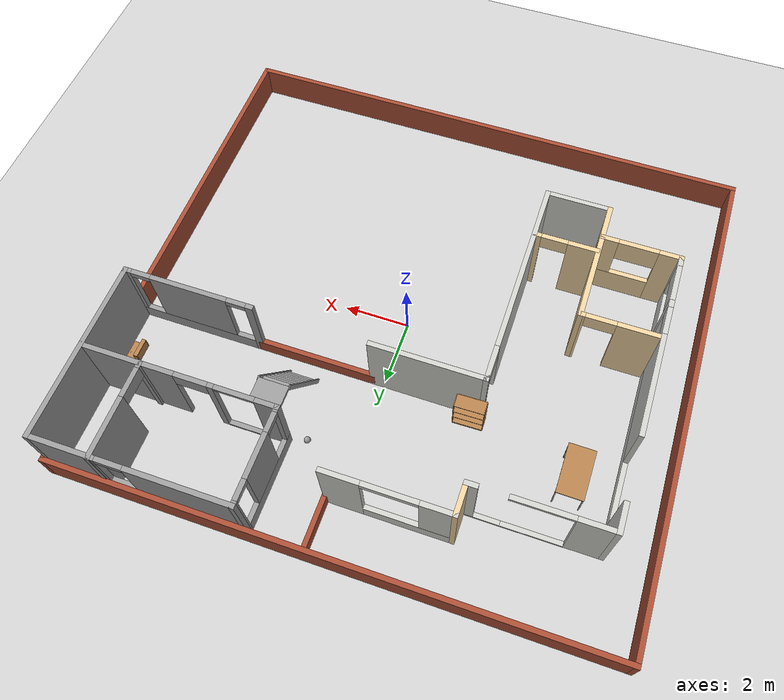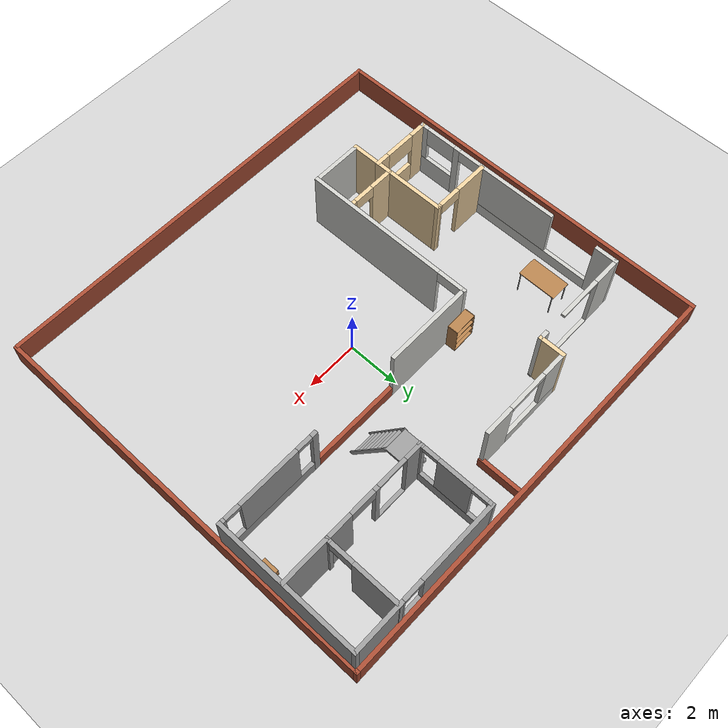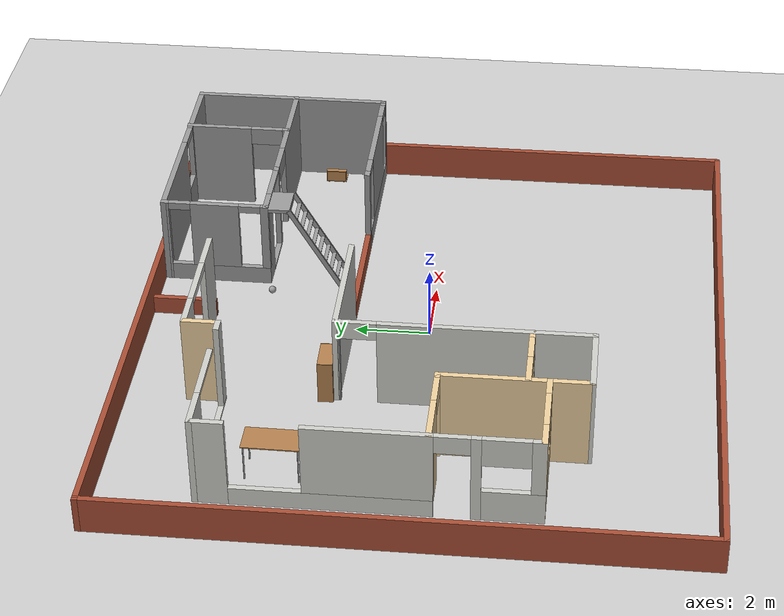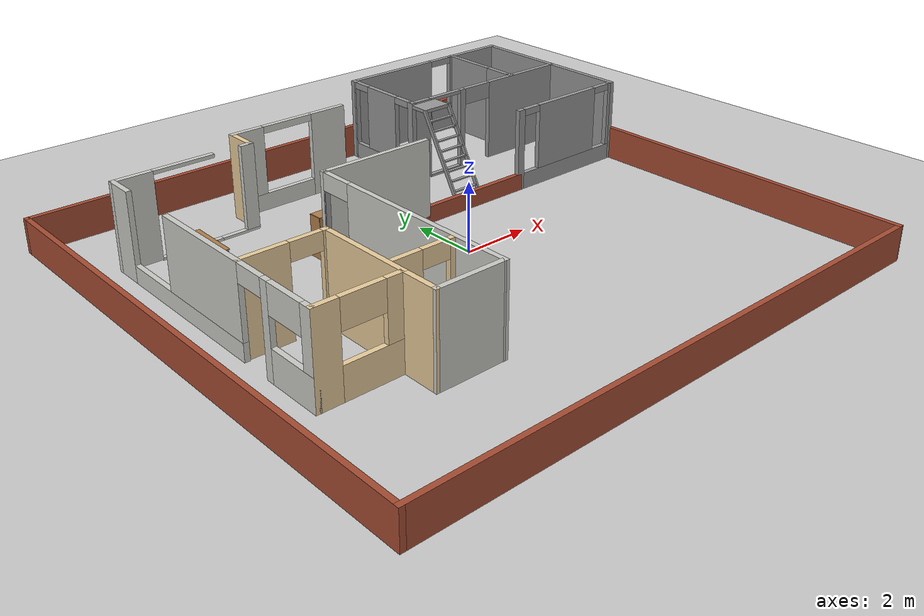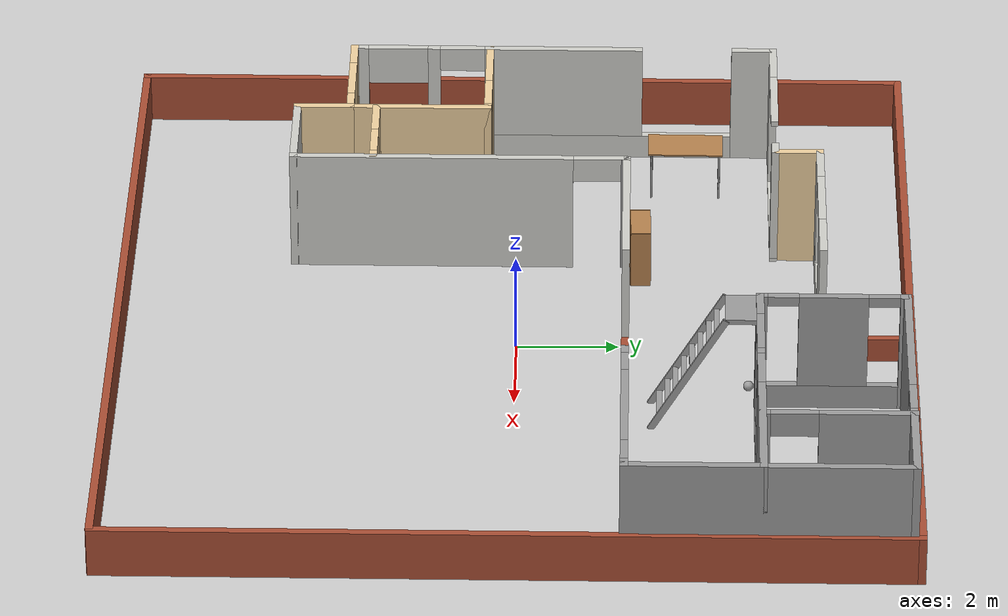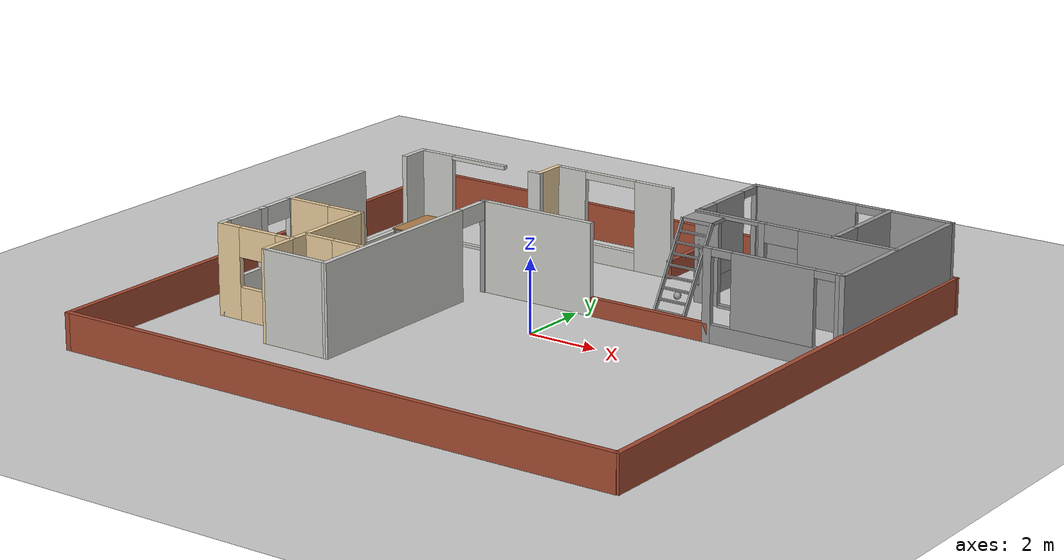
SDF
<sdf version="1.6">
 <world name="default">
  <plugin name="welcome" filename="libwelcome.so"/>
  <light name="sun" type="directional">
   <pose>0 0 10 0 -0 0</pose>
   <diffuse>0.8 0.8 0.8 1</diffuse>
   <specular>0.1 0.1 0.1 1</specular>
   <attenuation>
    <range>1000</range>
    <constant>0.9</constant>
    <linear>0.01</linear>
    <quadratic>0.001</quadratic>
   </attenuation>
   <direction>-0.5 0.5 -1</direction>
  </light>
  <model name="ground_plane">
   <static>1</static>
   <link name="link">
    <collision name="collision">
     <geometry><plane><normal>0 0 1</normal><size>100 100</size></plane></geometry>
     <surface>
      <contact><collide_bitmask>65535</collide_bitmask></contact>
      <friction><ode><mu>100</mu><mu2>50</mu2></ode></friction>
     </surface>
    </collision>
    <visual name="visual">
     <cast_shadows>0</cast_shadows>
     <geometry><plane><normal>0 0 1</normal><size>100 100</size></plane></geometry>
     <material>
      <script><uri>file://media/materials/scripts/gazebo.material</uri><name>Gazebo/Grey</name></script>
     </material>
    </visual>
   </link>
  </model>
  <gravity>0 0 -9.8</gravity>
  <magnetic_field>6e-06 2.3e-05 -4.2e-05</magnetic_field>
  <atmosphere type="adiabatic"/>
  <physics name="default_physics" default="0" type="ode">
   <max_step_size>0.001</max_step_size>
   <real_time_factor>1</real_time_factor>
   <real_time_update_rate>1000</real_time_update_rate>
  </physics>
  <scene><ambient>0.4 0.4 0.4 1</ambient><background>0.7 0.7 0.7 1</background><shadows>1</shadows></scene>
  <spherical_coordinates>
   <surface_model>EARTH_WGS84</surface_model>
   <latitude_deg>0</latitude_deg>
   <longitude_deg>0</longitude_deg>
   <elevation>0</elevation>
   <heading_deg>0</heading_deg>
  </spherical_coordinates>
  <model name="pongrut_house">
   <pose>-0.329079 -0.04 0 0 -0 0</pose>
   <link name="Wall_0">
    <collision name="Wall_0_Collision">
     <geometry><box><size>16.7231 0.15 1</size></box></geometry>
     <pose>0 0 0.5 0 -0 0</pose>
    </collision>
    <visual name="Wall_0_Visual">
     <pose>0 0 0.5 0 -0 0</pose>
     <geometry><box><size>16.7231 0.15 1</size></box></geometry>
     <material>
      <script><uri>file://media/materials/scripts/gazebo.material</uri><name>Gazebo/Bricks</name></script>
      <ambient>1 1 1 1</ambient>
     </material>
     <meta><layer>0</layer></meta>
    </visual>
    <pose>0 7.70141 0 0 -0 0</pose>
   </link>
   <link name="Wall_18">
    <pose>-1.19963 5.9806 0 0 -0 3.14149</pose>
    <visual name="Wall_18_Visual_0">
     <pose>-1.31206 0 1.25 0 -0 0</pose>
     <geometry><box><size>1.16383 0.15 2.5</size></box></geometry>
     <material>
      <script><uri>file://media/materials/scripts/gazebo.material</uri><name>Gazebo/CeilingTiled</name></script>
      <ambient>0.921569 0.807843 0.615686 1</ambient>
     </material>
     <meta><layer>0</layer></meta>
    </visual>
    <collision name="Wall_18_Collision_0">
     <geometry><box><size>1.16383 0.15 2.5</size></box></geometry>
     <pose>-1.31206 0 1.25 0 -0 0</pose>
    </collision>
    <visual name="Wall_18_Visual_1">
     <pose>0.581912 0 0.25 0 -0 0</pose>
     <geometry><box><size>2.62412 0.15 0.5</size></box></geometry>
     <material>
      <script><uri>file://media/materials/scripts/gazebo.material</uri><name>Gazebo/CeilingTiled</name></script>
      <ambient>0.921569 0.807843 0.615686 1</ambient>
     </material>
     <meta><layer>0</layer></meta>
    </visual>
    <collision name="Wall_18_Collision_1">
     <geometry><box><size>2.62412 0.15 0.5</size></box></geometry>
     <pose>0.581912 0 0.25 0 -0 0</pose>
    </collision>
    <visual name="Wall_18_Visual_2">
     <pose>1.38191 0 1.5 0 -0 0</pose>
     <geometry><box><size>1.02412 0.15 2</size></box></geometry>
     <material>
      <script><uri>file://media/materials/scripts/gazebo.material</uri><name>Gazebo/CeilingTiled</name></script>
      <ambient>0.921569 0.807843 0.615686 1</ambient>
     </material>
     <meta><layer>0</layer></meta>
    </visual>
    <collision name="Wall_18_Collision_2">
     <geometry><box><size>1.02412 0.15 2</size></box></geometry>
     <pose>1.38191 0 1.5 0 -0 0</pose>
    </collision>
    <visual name="Wall_18_Visual_3">
     <pose>0.069851 0 2.4 0 -0 0</pose>
     <geometry><box><size>1.6 0.15 0.2</size></box></geometry>
     <material>
      <script><uri>file://media/materials/scripts/gazebo.material</uri><name>Gazebo/CeilingTiled</name></script>
      <ambient>0.921569 0.807843 0.615686 1</ambient>
     </material>
     <meta><layer>0</layer></meta>
    </visual>
    <collision name="Wall_18_Collision_3">
     <geometry><box><size>1.6 0.15 0.2</size></box></geometry>
     <pose>0.069851 0 2.4 0 -0 0</pose>
    </collision>
   </link>
   <link name="Wall_22">
    <pose>-6.96881 0.867525 0 0 0 -1.5708</pose>
    <visual name="Wall_22_Visual_0">
     <pose>-3.85377 0 1.25 0 -0 0</pose>
     <geometry><box><size>0.910059 0.15 2.5</size></box></geometry>
     <material>
      <script><uri>file://media/materials/scripts/gazebo.material</uri><name>Gazebo/CeilingTiled</name></script>
      <ambient>0.921569 0.807843 0.615686 1</ambient>
     </material>
     <meta><layer>0</layer></meta>
    </visual>
    <collision name="Wall_22_Collision_0">
     <geometry><box><size>0.910059 0.15 2.5</size></box></geometry>
     <pose>-3.85377 0 1.25 0 -0 0</pose>
    </collision>
    <visual name="Wall_22_Visual_1">
     <pose>2.62377 0 1.25 0 -0 0</pose>
     <geometry><box><size>0.252126 0.15 2.5</size></box></geometry>
     <material>
      <script><uri>file://media/materials/scripts/gazebo.material</uri><name>Gazebo/CeilingTiled</name></script>
      <ambient>0.921569 0.807843 0.615686 1</ambient>
     </material>
     <meta><layer>0</layer></meta>
    </visual>
    <collision name="Wall_22_Collision_1">
     <geometry><box><size>0.252126 0.15 2.5</size></box></geometry>
     <pose>2.62377 0 1.25 0 -0 0</pose>
    </collision>
    <visual name="Wall_22_Visual_2">
     <pose>-0.900517 0 0.25 0 -0 0</pose>
     <geometry><box><size>4.99644 0.15 0.5</size></box></geometry>
     <material>
      <script><uri>file://media/materials/scripts/gazebo.material</uri><name>Gazebo/CeilingTiled</name></script>
      <ambient>0.921569 0.807843 0.615686 1</ambient>
     </material>
     <meta><layer>0</layer></meta>
    </visual>
    <collision name="Wall_22_Collision_2">
     <geometry><box><size>4.99644 0.15 0.5</size></box></geometry>
     <pose>-0.900517 0 0.25 0 -0 0</pose>
    </collision>
    <visual name="Wall_22_Visual_3">
     <pose>3.52931 0 0.45 0 -0 0</pose>
     <geometry><box><size>1.55897 0.15 0.9</size></box></geometry>
     <material>
      <script><uri>file://media/materials/scripts/gazebo.material</uri><name>Gazebo/CeilingTiled</name></script>
      <ambient>0.921569 0.807843 0.615686 1</ambient>
     </material>
     <meta><layer>0</layer></meta>
    </visual>
    <collision name="Wall_22_Collision_3">
     <geometry><box><size>1.55897 0.15 0.9</size></box></geometry>
     <pose>3.52931 0 0.45 0 -0 0</pose>
    </collision>
    <visual name="Wall_22_Visual_4">
     <pose>-0.000517 0 1.5 0 -0 0</pose>
     <geometry><box><size>3.19644 0.15 2</size></box></geometry>
     <material>
      <script><uri>file://media/materials/scripts/gazebo.material</uri><name>Gazebo/CeilingTiled</name></script>
      <ambient>0.921569 0.807843 0.615686 1</ambient>
     </material>
     <meta><layer>0</layer></meta>
    </visual>
    <collision name="Wall_22_Collision_4">
     <geometry><box><size>3.19644 0.15 2</size></box></geometry>
     <pose>-0.000517 0 1.5 0 -0 0</pose>
    </collision>
    <visual name="Wall_22_Visual_5">
     <pose>4.12931 0 1.7 0 -0 0</pose>
     <geometry><box><size>0.358966 0.15 1.6</size></box></geometry>
     <material>
      <script><uri>file://media/materials/scripts/gazebo.material</uri><name>Gazebo/CeilingTiled</name></script>
      <ambient>0.921569 0.807843 0.615686 1</ambient>
     </material>
     <meta><layer>0</layer></meta>
    </visual>
    <collision name="Wall_22_Collision_5">
     <geometry><box><size>0.358966 0.15 1.6</size></box></geometry>
     <pose>4.12931 0 1.7 0 -0 0</pose>
    </collision>
    <visual name="Wall_22_Visual_6">
     <pose>3.34983 0 2.1 0 -0 0</pose>
     <geometry><box><size>1.2 0.15 0.8</size></box></geometry>
     <material>
      <script><uri>file://media/materials/scripts/gazebo.material</uri><name>Gazebo/CeilingTiled</name></script>
      <ambient>0.921569 0.807843 0.615686 1</ambient>
     </material>
     <meta><layer>0</layer></meta>
    </visual>
    <collision name="Wall_22_Collision_6">
     <geometry><box><size>1.2 0.15 0.8</size></box></geometry>
     <pose>3.34983 0 2.1 0 -0 0</pose>
    </collision>
    <visual name="Wall_22_Visual_7">
     <pose>2.0477 0 2.25 0 -0 0</pose>
     <geometry><box><size>0.9 0.15 0.5</size></box></geometry>
     <material>
      <script><uri>file://media/materials/scripts/gazebo.material</uri><name>Gazebo/CeilingTiled</name></script>
      <ambient>0.921569 0.807843 0.615686 1</ambient>
     </material>
     <meta><layer>0</layer></meta>
    </visual>
    <collision name="Wall_22_Collision_7">
     <geometry><box><size>0.9 0.15 0.5</size></box></geometry>
     <pose>2.0477 0 2.25 0 -0 0</pose>
    </collision>
   </link>
   <link name="Wall_26">
    <collision name="Wall_26_Collision">
     <geometry><box><size>1.01188 0.15 2.5</size></box></geometry>
     <pose>0 0 1.25 0 -0 0</pose>
    </collision>
    <visual name="Wall_26_Visual">
     <pose>0 0 1.25 0 -0 0</pose>
     <geometry><box><size>1.01188 0.15 2.5</size></box></geometry>
     <material>
      <script><uri>file://media/materials/scripts/gazebo.material</uri><name>Gazebo/Grey</name></script>
      <ambient>0.921569 0.807843 0.615686 1</ambient>
     </material>
     <meta><layer>0</layer></meta>
    </visual>
    <pose>-3.0188 5.54989 0 0 0 -1.5709</pose>
   </link>
   <link name="Wall_28">
    <pose>-5.79381 -3.36627 0 0 -0 0</pose>
    <visual name="Wall_28_Visual_0">
     <pose>-0.887893 0 1.25 0 -0 0</pose>
     <geometry><box><size>0.724215 0.15 2.5</size></box></geometry>
     <material>
      <script><uri>file://media/materials/scripts/gazebo.material</uri><name>Gazebo/Grey</name></script>
      <ambient>0.921569 0.807843 0.615686 1</ambient>
     </material>
     <meta><layer>0</layer></meta>
    </visual>
    <collision name="Wall_28_Collision_0">
     <geometry><box><size>0.724215 0.15 2.5</size></box></geometry>
     <pose>-0.887893 0 1.25 0 -0 0</pose>
    </collision>
    <visual name="Wall_28_Visual_1">
     <pose>0.362107 0 0.45 0 -0 0</pose>
     <geometry><box><size>1.77578 0.15 0.9</size></box></geometry>
     <material>
      <script><uri>file://media/materials/scripts/gazebo.material</uri><name>Gazebo/Grey</name></script>
      <ambient>0.921569 0.807843 0.615686 1</ambient>
     </material>
     <meta><layer>0</layer></meta>
    </visual>
    <collision name="Wall_28_Collision_1">
     <geometry><box><size>1.77578 0.15 0.9</size></box></geometry>
     <pose>0.362107 0 0.45 0 -0 0</pose>
    </collision>
    <visual name="Wall_28_Visual_2">
     <pose>0.962107 0 1.7 0 -0 0</pose>
     <geometry><box><size>0.575785 0.15 1.6</size></box></geometry>
     <material>
      <script><uri>file://media/materials/scripts/gazebo.material</uri><name>Gazebo/Grey</name></script>
      <ambient>0.921569 0.807843 0.615686 1</ambient>
     </material>
     <meta><layer>0</layer></meta>
    </visual>
    <collision name="Wall_28_Collision_2">
     <geometry><box><size>0.575785 0.15 1.6</size></box></geometry>
     <pose>0.962107 0 1.7 0 -0 0</pose>
    </collision>
    <visual name="Wall_28_Visual_3">
     <pose>0.074215 0 2.1 0 -0 0</pose>
     <geometry><box><size>1.2 0.15 0.8</size></box></geometry>
     <material>
      <script><uri>file://media/materials/scripts/gazebo.material</uri><name>Gazebo/Grey</name></script>
      <ambient>0.921569 0.807843 0.615686 1</ambient>
     </material>
     <meta><layer>0</layer></meta>
    </visual>
    <collision name="Wall_28_Collision_3">
     <geometry><box><size>1.2 0.15 0.8</size></box></geometry>
     <pose>0.074215 0 2.1 0 -0 0</pose>
    </collision>
   </link>
   <link name="Wall_3">
    <collision name="Wall_3_Collision">
     <geometry><box><size>15.5531 0.15 1</size></box></geometry>
     <pose>0 0 0.5 0 -0 0</pose>
    </collision>
    <visual name="Wall_3_Visual">
     <pose>0 0 0.5 0 -0 0</pose>
     <geometry><box><size>15.5531 0.15 1</size></box></geometry>
     <material>
      <script><uri>file://media/materials/scripts/gazebo.material</uri><name>Gazebo/Bricks</name></script>
      <ambient>1 1 1 1</ambient>
     </material>
     <meta><layer>0</layer></meta>
    </visual>
    <pose>-8.2865 -9.3e-05 0 0 0 -1.5708</pose>
   </link>
   <link name="Wall_30">
    <collision name="Wall_30_Collision">
     <geometry><box><size>1.2 0.15 2.5</size></box></geometry>
     <pose>0 0 1.25 0 -0 0</pose>
    </collision>
    <visual name="Wall_30_Visual">
     <pose>0 0 1.25 0 -0 0</pose>
     <geometry><box><size>1.2 0.15 2.5</size></box></geometry>
     <material>
      <script><uri>file://media/materials/scripts/gazebo.material</uri><name>Gazebo/Grey</name></script>
      <ambient>0.921569 0.807843 0.615686 1</ambient>
     </material>
     <meta><layer>0</layer></meta>
    </visual>
    <pose>-4.61881 -3.89127 0 0 0 -1.5708</pose>
   </link>
   <link name="Wall_32">
    <collision name="Wall_32_Collision">
     <geometry><box><size>2.08231 0.15 2.5</size></box></geometry>
     <pose>0 0 1.25 0 -0 0</pose>
    </collision>
    <visual name="Wall_32_Visual">
     <pose>0 0 1.25 0 -0 0</pose>
     <geometry><box><size>2.08231 0.15 2.5</size></box></geometry>
     <material>
      <script><uri>file://media/materials/scripts/gazebo.material</uri><name>Gazebo/CeilingTiled</name></script>
      <ambient>0.921569 0.807843 0.615686 1</ambient>
     </material>
     <meta><layer>0</layer></meta>
    </visual>
    <pose>-3.65266 -4.41643 0 0 0 -0.000168</pose>
   </link>
   <link name="Wall_39">
    <pose>-4.99381 5.10132 0 0 -0 0</pose>
    <visual name="Wall_39_Visual_0">
     <pose>-1.48216 0 1.25 0 -0 0</pose>
     <geometry><box><size>1.13568 0.15 2.5</size></box></geometry>
     <material>
      <script><uri>file://media/materials/scripts/gazebo.material</uri><name>Gazebo/CeilingTiled</name></script>
      <ambient>0.921569 0.807843 0.615686 1</ambient>
     </material>
     <meta><layer>0</layer></meta>
    </visual>
    <collision name="Wall_39_Collision_0">
     <geometry><box><size>1.13568 0.15 2.5</size></box></geometry>
     <pose>-1.48216 0 1.25 0 -0 0</pose>
    </collision>
    <visual name="Wall_39_Visual_1">
     <pose>1.46784 0 0 0 -0 0</pose>
     <geometry><box><size>1.16432 0.15 0.1</size></box></geometry>
     <material>
      <script><uri>file://media/materials/scripts/gazebo.material</uri><name>Gazebo/CeilingTiled</name></script>
      <ambient>0.921569 0.807843 0.615686 1</ambient>
     </material>
     <meta><layer>0</layer></meta>
    </visual>
    <collision name="Wall_39_Collision_1">
     <geometry><box><size>1.16432 0.15 0.1</size></box></geometry>
     <pose>1.46784 0 0 0 -0 0</pose>
    </collision>
    <visual name="Wall_39_Visual_2">
     <pose>1.849 0 1.25 0 -0 0</pose>
     <geometry><box><size>0.401995 0.15 2.5</size></box></geometry>
     <material>
      <script><uri>file://media/materials/scripts/gazebo.material</uri><name>Gazebo/CeilingTiled</name></script>
      <ambient>0.921569 0.807843 0.615686 1</ambient>
     </material>
     <meta><layer>0</layer></meta>
    </visual>
    <collision name="Wall_39_Collision_2">
     <geometry><box><size>0.401995 0.15 2.5</size></box></geometry>
     <pose>1.849 0 1.25 0 -0 0</pose>
    </collision>
    <visual name="Wall_39_Visual_3">
     <pose>-0.014321 0 0 0 -0 0</pose>
     <geometry><box><size>1.8 0.15 0.1</size></box></geometry>
     <material>
      <script><uri>file://media/materials/scripts/gazebo.material</uri><name>Gazebo/CeilingTiled</name></script>
      <ambient>0.921569 0.807843 0.615686 1</ambient>
     </material>
     <meta><layer>0</layer></meta>
    </visual>
    <collision name="Wall_39_Collision_3">
     <geometry><box><size>1.8 0.15 0.1</size></box></geometry>
     <pose>-0.014321 0 0 0 -0 0</pose>
    </collision>
    <visual name="Wall_39_Visual_4">
     <pose>1.849 0 1.25 0 -0 0</pose>
     <geometry><box><size>0.401995 0.15 2.5</size></box></geometry>
     <material>
      <script><uri>file://media/materials/scripts/gazebo.material</uri><name>Gazebo/CeilingTiled</name></script>
      <ambient>0.921569 0.807843 0.615686 1</ambient>
     </material>
     <meta><layer>0</layer></meta>
    </visual>
    <collision name="Wall_39_Collision_4">
     <geometry><box><size>0.401995 0.15 2.5</size></box></geometry>
     <pose>1.849 0 1.25 0 -0 0</pose>
    </collision>
    <visual name="Wall_39_Visual_5">
     <pose>-0.033158 0 2.45 0 -0 0</pose>
     <geometry><box><size>1.76233 0.15 0.1</size></box></geometry>
     <material>
      <script><uri>file://media/materials/scripts/gazebo.material</uri><name>Gazebo/CeilingTiled</name></script>
      <ambient>0.921569 0.807843 0.615686 1</ambient>
     </material>
     <meta><layer>0</layer></meta>
    </visual>
    <collision name="Wall_39_Collision_5">
     <geometry><box><size>1.76233 0.15 0.1</size></box></geometry>
     <pose>-0.033158 0 2.45 0 -0 0</pose>
    </collision>
   </link>
   <link name="Wall_45">
    <pose>-2.6865 -1.12509 0 0 -0 1.5708</pose>
    <visual name="Wall_45_Visual_0">
     <pose>-0.565074 0 1.25 0 -0 0</pose>
     <geometry><box><size>5.60285 0.15 2.5</size></box></geometry>
     <material>
      <script><uri>file://media/materials/scripts/gazebo.material</uri><name>Gazebo/CeilingTiled</name></script>
      <ambient>0.921569 0.807843 0.615686 1</ambient>
     </material>
     <meta><layer>0</layer></meta>
    </visual>
    <collision name="Wall_45_Collision_0">
     <geometry><box><size>5.60285 0.15 2.5</size></box></geometry>
     <pose>-0.565074 0 1.25 0 -0 0</pose>
    </collision>
    <visual name="Wall_45_Visual_1">
     <pose>3.30143 0 1.25 0 -0 0</pose>
     <geometry><box><size>0.130149 0.15 2.5</size></box></geometry>
     <material>
      <script><uri>file://media/materials/scripts/gazebo.material</uri><name>Gazebo/CeilingTiled</name></script>
      <ambient>0.921569 0.807843 0.615686 1</ambient>
     </material>
     <meta><layer>0</layer></meta>
    </visual>
    <collision name="Wall_45_Collision_1">
     <geometry><box><size>0.130149 0.15 2.5</size></box></geometry>
     <pose>3.30143 0 1.25 0 -0 0</pose>
    </collision>
    <visual name="Wall_45_Visual_2">
     <pose>2.73635 0 2.25 0 -0 0</pose>
     <geometry><box><size>1 0.15 0.5</size></box></geometry>
     <material>
      <script><uri>file://media/materials/scripts/gazebo.material</uri><name>Gazebo/CeilingTiled</name></script>
      <ambient>0.921569 0.807843 0.615686 1</ambient>
     </material>
     <meta><layer>0</layer></meta>
    </visual>
    <collision name="Wall_45_Collision_2">
     <geometry><box><size>1 0.15 0.5</size></box></geometry>
     <pose>2.73635 0 2.25 0 -0 0</pose>
    </collision>
   </link>
   <link name="Wall_5">
    <collision name="Wall_5_Collision">
     <geometry><box><size>15.5374 0.15 1</size></box></geometry>
     <pose>0 0 0.5 0 -0 0</pose>
    </collision>
    <visual name="Wall_5_Visual">
     <pose>0 0 0.5 0 -0 0</pose>
     <geometry><box><size>15.5374 0.15 1</size></box></geometry>
     <material>
      <script><uri>file://media/materials/scripts/gazebo.material</uri><name>Gazebo/Bricks</name></script>
      <ambient>1 1 1 1</ambient>
     </material>
     <meta><layer>0</layer></meta>
    </visual>
    <pose>8.2865 0.007907 0 0 0 -1.5708</pose>
   </link>
   <link name="Wall_54">
    <collision name="Wall_54_Collision">
     <geometry><box><size>0.186 0.15 2.5</size></box></geometry>
     <pose>0 0 1.25 0 -0 0</pose>
    </collision>
    <visual name="Wall_54_Visual">
     <pose>0 0 1.25 0 -0 0</pose>
     <geometry><box><size>0.186 0.15 2.5</size></box></geometry>
     <material>
      <script><uri>file://media/materials/scripts/gazebo.material</uri><name>Gazebo/Grey</name></script>
      <ambient>1 1 1 1</ambient>
     </material>
     <meta><layer>0</layer></meta>
    </visual>
    <pose>-2.6865 2.14841 0 0 0 -1.5708</pose>
   </link>
   <link name="Wall_59">
    <collision name="Wall_59_Collision">
     <geometry><box><size>3.5 0.15 2.5</size></box></geometry>
     <pose>0 0 1.25 0 -0 0</pose>
    </collision>
    <visual name="Wall_59_Visual">
     <pose>0 0 1.25 0 -0 0</pose>
     <geometry><box><size>3.5 0.15 2.5</size></box></geometry>
     <material>
      <script><uri>file://media/materials/scripts/gazebo.material</uri><name>Gazebo/CeilingTiled</name></script>
      <ambient>0.921569 0.807843 0.615686 1</ambient>
     </material>
     <meta><layer>0</layer></meta>
    </visual>
    <pose>-1.0115 2.16641 0 0 -0 0</pose>
   </link>
   <link name="Wall_62">
    <collision name="Wall_62_Collision">
     <geometry><box><size>2.9 0.15 2.5</size></box></geometry>
     <pose>0 0 1.25 0 -0 0</pose>
    </collision>
    <visual name="Wall_62_Visual">
     <pose>0 0 1.25 0 -0 0</pose>
     <geometry><box><size>2.9 0.15 2.5</size></box></geometry>
     <material>
      <script><uri>file://media/materials/scripts/gazebo.material</uri><name>Gazebo/Grey</name></script>
      <ambient>0.921569 0.807843 0.615686 1</ambient>
     </material>
     <meta><layer>0</layer></meta>
    </visual>
    <pose>-4.61881 -1.99127 0 0 -0 1.5708</pose>
   </link>
   <link name="Wall_64">
    <pose>-5.79381 -0.616269 0 0 -0 3.14159</pose>
    <visual name="Wall_64_Visual_0">
     <pose>-1.14338 0 1.25 0 -0 0</pose>
     <geometry><box><size>0.213234 0.15 2.5</size></box></geometry>
     <material>
      <script><uri>file://media/materials/scripts/gazebo.material</uri><name>Gazebo/Grey</name></script>
      <ambient>0.921569 0.807843 0.615686 1</ambient>
     </material>
     <meta><layer>0</layer></meta>
    </visual>
    <collision name="Wall_64_Collision_0">
     <geometry><box><size>0.213234 0.15 2.5</size></box></geometry>
     <pose>-1.14338 0 1.25 0 -0 0</pose>
    </collision>
    <visual name="Wall_64_Visual_1">
     <pose>0.556617 0 1.25 0 -0 0</pose>
     <geometry><box><size>1.38677 0.15 2.5</size></box></geometry>
     <material>
      <script><uri>file://media/materials/scripts/gazebo.material</uri><name>Gazebo/Grey</name></script>
      <ambient>0.921569 0.807843 0.615686 1</ambient>
     </material>
     <meta><layer>0</layer></meta>
    </visual>
    <collision name="Wall_64_Collision_1">
     <geometry><box><size>1.38677 0.15 2.5</size></box></geometry>
     <pose>0.556617 0 1.25 0 -0 0</pose>
    </collision>
    <visual name="Wall_64_Visual_2">
     <pose>-0.586766 0 2.25 0 -0 0</pose>
     <geometry><box><size>0.9 0.15 0.5</size></box></geometry>
     <material>
      <script><uri>file://media/materials/scripts/gazebo.material</uri><name>Gazebo/Grey</name></script>
      <ambient>0.921569 0.807843 0.615686 1</ambient>
     </material>
     <meta><layer>0</layer></meta>
    </visual>
    <collision name="Wall_64_Collision_2">
     <geometry><box><size>0.9 0.15 0.5</size></box></geometry>
     <pose>-0.586766 0 2.25 0 -0 0</pose>
    </collision>
   </link>
   <link name="Wall_7">
    <collision name="Wall_7_Collision">
     <geometry><box><size>16.653 0.15 1</size></box></geometry>
     <pose>0 0 0.5 0 -0 0</pose>
    </collision>
    <visual name="Wall_7_Visual">
     <pose>0 0 0.5 0 -0 0</pose>
     <geometry><box><size>16.653 0.15 1</size></box></geometry>
     <material>
      <script><uri>file://media/materials/scripts/gazebo.material</uri><name>Gazebo/Bricks</name></script>
      <ambient>1 1 1 1</ambient>
     </material>
     <meta><layer>0</layer></meta>
    </visual>
    <pose>-0.035 -7.70159 0 0 -0 0</pose>
   </link>
   <link name="Wall_72">
    <pose>6.2085 2.16641 0 0 -0 0</pose>
    <visual name="Wall_72_Visual_0">
     <pose>-1.93039 0 1.25 0 -0 0</pose>
     <geometry><box><size>0.239214 0.15 2.5</size></box></geometry>
     <material>
      <script><uri>file://media/materials/scripts/gazebo.material</uri><name>Gazebo/Grey</name></script>
      <ambient>0.372549 0.372549 0.372549 1</ambient>
     </material>
     <meta><layer>0</layer></meta>
    </visual>
    <collision name="Wall_72_Collision_0">
     <geometry><box><size>0.239214 0.15 2.5</size></box></geometry>
     <pose>-1.93039 0 1.25 0 -0 0</pose>
    </collision>
    <visual name="Wall_72_Visual_1">
     <pose>0.119607 0 0.25 0 -0 0</pose>
     <geometry><box><size>3.86079 0.15 0.5</size></box></geometry>
     <material>
      <script><uri>file://media/materials/scripts/gazebo.material</uri><name>Gazebo/Grey</name></script>
      <ambient>0.372549 0.372549 0.372549 1</ambient>
     </material>
     <meta><layer>0</layer></meta>
    </visual>
    <collision name="Wall_72_Collision_1">
     <geometry><box><size>3.86079 0.15 0.5</size></box></geometry>
     <pose>0.119607 0 0.25 0 -0 0</pose>
    </collision>
    <visual name="Wall_72_Visual_2">
     <pose>-0.013929 0 1.5 0 -0 0</pose>
     <geometry><box><size>2.39371 0.15 2</size></box></geometry>
     <material>
      <script><uri>file://media/materials/scripts/gazebo.material</uri><name>Gazebo/Grey</name></script>
      <ambient>0.372549 0.372549 0.372549 1</ambient>
     </material>
     <meta><layer>0</layer></meta>
    </visual>
    <collision name="Wall_72_Collision_2">
     <geometry><box><size>2.39371 0.15 2</size></box></geometry>
     <pose>-0.013929 0 1.5 0 -0 0</pose>
    </collision>
    <visual name="Wall_72_Visual_3">
     <pose>1.91646 0 1.5 0 -0 0</pose>
     <geometry><box><size>0.267073 0.15 2</size></box></geometry>
     <material>
      <script><uri>file://media/materials/scripts/gazebo.material</uri><name>Gazebo/Grey</name></script>
      <ambient>0.372549 0.372549 0.372549 1</ambient>
     </material>
     <meta><layer>0</layer></meta>
    </visual>
    <collision name="Wall_72_Collision_3">
     <geometry><box><size>0.267073 0.15 2</size></box></geometry>
     <pose>1.91646 0 1.5 0 -0 0</pose>
    </collision>
    <visual name="Wall_72_Visual_4">
     <pose>-1.51079 0 2.4 0 -0 0</pose>
     <geometry><box><size>0.6 0.15 0.2</size></box></geometry>
     <material>
      <script><uri>file://media/materials/scripts/gazebo.material</uri><name>Gazebo/Grey</name></script>
      <ambient>0.372549 0.372549 0.372549 1</ambient>
     </material>
     <meta><layer>0</layer></meta>
    </visual>
    <collision name="Wall_72_Collision_4">
     <geometry><box><size>0.6 0.15 0.2</size></box></geometry>
     <pose>-1.51079 0 2.4 0 -0 0</pose>
    </collision>
    <visual name="Wall_72_Visual_5">
     <pose>1.48293 0 2.4 0 -0 0</pose>
     <geometry><box><size>0.6 0.15 0.2</size></box></geometry>
     <material>
      <script><uri>file://media/materials/scripts/gazebo.material</uri><name>Gazebo/Grey</name></script>
      <ambient>0.372549 0.372549 0.372549 1</ambient>
     </material>
     <meta><layer>0</layer></meta>
    </visual>
    <collision name="Wall_72_Collision_5">
     <geometry><box><size>0.6 0.15 0.2</size></box></geometry>
     <pose>1.48293 0 2.4 0 -0 0</pose>
    </collision>
   </link>
   <link name="Wall_76">
    <pose>5.2585 7.55141 0 0 -0 0</pose>
    <visual name="Wall_76_Visual_0">
     <pose>-1.42413 0 1.25 0 -0 0</pose>
     <geometry><box><size>3.15174 0.15 2.5</size></box></geometry>
     <material>
      <script><uri>file://media/materials/scripts/gazebo.material</uri><name>Gazebo/Grey</name></script>
      <ambient>0.372549 0.372549 0.372549 1</ambient>
     </material>
     <meta><layer>0</layer></meta>
    </visual>
    <collision name="Wall_76_Collision_0">
     <geometry><box><size>3.15174 0.15 2.5</size></box></geometry>
     <pose>-1.42413 0 1.25 0 -0 0</pose>
    </collision>
    <visual name="Wall_76_Visual_1">
     <pose>1.57587 0 0.45 0 -0 0</pose>
     <geometry><box><size>2.84826 0.15 0.9</size></box></geometry>
     <material>
      <script><uri>file://media/materials/scripts/gazebo.material</uri><name>Gazebo/Grey</name></script>
      <ambient>0.372549 0.372549 0.372549 1</ambient>
     </material>
     <meta><layer>0</layer></meta>
    </visual>
    <collision name="Wall_76_Collision_1">
     <geometry><box><size>2.84826 0.15 0.9</size></box></geometry>
     <pose>1.57587 0 0.45 0 -0 0</pose>
    </collision>
    <visual name="Wall_76_Visual_2">
     <pose>1.97587 0 1.7 0 -0 0</pose>
     <geometry><box><size>2.04826 0.15 1.6</size></box></geometry>
     <material>
      <script><uri>file://media/materials/scripts/gazebo.material</uri><name>Gazebo/Grey</name></script>
      <ambient>0.372549 0.372549 0.372549 1</ambient>
     </material>
     <meta><layer>0</layer></meta>
    </visual>
    <collision name="Wall_76_Collision_2">
     <geometry><box><size>2.04826 0.15 1.6</size></box></geometry>
     <pose>1.97587 0 1.7 0 -0 0</pose>
    </collision>
    <visual name="Wall_76_Visual_3">
     <pose>0.551743 0 2.4 0 -0 0</pose>
     <geometry><box><size>0.8 0.15 0.2</size></box></geometry>
     <material>
      <script><uri>file://media/materials/scripts/gazebo.material</uri><name>Gazebo/Grey</name></script>
      <ambient>0.372549 0.372549 0.372549 1</ambient>
     </material>
     <meta><layer>0</layer></meta>
    </visual>
    <collision name="Wall_76_Collision_3">
     <geometry><box><size>0.8 0.15 0.2</size></box></geometry>
     <pose>0.551743 0 2.4 0 -0 0</pose>
    </collision>
   </link>
   <link name="Wall_78">
    <collision name="Wall_78_Collision">
     <geometry><box><size>5.53521 0.15 2.5</size></box></geometry>
     <pose>0 0 1.25 0 -0 0</pose>
    </collision>
    <visual name="Wall_78_Visual">
     <pose>0 0 1.25 0 -0 0</pose>
     <geometry><box><size>5.53521 0.15 2.5</size></box></geometry>
     <material>
      <script><uri>file://media/materials/scripts/gazebo.material</uri><name>Gazebo/Grey</name></script>
      <ambient>0.372549 0.372549 0.372549 1</ambient>
     </material>
     <meta><layer>0</layer></meta>
    </visual>
    <pose>8.1835 4.85891 0 0 -0 1.5708</pose>
   </link>
   <link name="Wall_80">
    <collision name="Wall_80_Collision">
     <geometry><box><size>1.75 0.15 0.5</size></box></geometry>
     <pose>0 0 0.25 0 -0 0</pose>
    </collision>
    <visual name="Wall_80_Visual">
     <pose>0 0 0.25 0 -0 0</pose>
     <geometry><box><size>1.75 0.15 0.5</size></box></geometry>
     <material>
      <script><uri>file://media/materials/scripts/gazebo.material</uri><name>Gazebo/Bricks</name></script>
      <ambient>1 1 1 1</ambient>
     </material>
     <meta><layer>0</layer></meta>
    </visual>
    <pose>0.6635 6.76641 0 0 -0 1.5708</pose>
   </link>
   <link name="Wall_82">
    <collision name="Wall_82_Collision">
     <geometry><box><size>3.72 0.15 0.5</size></box></geometry>
     <pose>0 0 0.25 0 -0 0</pose>
    </collision>
    <visual name="Wall_82_Visual">
     <pose>0 0 0.25 0 -0 0</pose>
     <geometry><box><size>3.72 0.15 0.5</size></box></geometry>
     <material>
      <script><uri>file://media/materials/scripts/gazebo.material</uri><name>Gazebo/Bricks</name></script>
      <ambient>1 1 1 1</ambient>
     </material>
     <meta><layer>0</layer></meta>
    </visual>
    <pose>2.4485 2.16641 0 0 -0 0</pose>
   </link>
   <link name="Wall_84">
    <pose>5.2585 4.73441 0 0 -0 0</pose>
    <visual name="Wall_84_Visual_0">
     <pose>-2.63758 0 1.25 0 -0 0</pose>
     <geometry><box><size>0.724843 0.15 2.5</size></box></geometry>
     <material>
      <script><uri>file://media/materials/scripts/gazebo.material</uri><name>Gazebo/Grey</name></script>
      <ambient>0.372549 0.372549 0.372549 1</ambient>
     </material>
     <meta><layer>0</layer></meta>
    </visual>
    <collision name="Wall_84_Collision_0">
     <geometry><box><size>0.724843 0.15 2.5</size></box></geometry>
     <pose>-2.63758 0 1.25 0 -0 0</pose>
    </collision>
    <visual name="Wall_84_Visual_1">
     <pose>-0.983144 0 1.25 0 -0 0</pose>
     <geometry><box><size>0.184025 0.15 2.5</size></box></geometry>
     <material>
      <script><uri>file://media/materials/scripts/gazebo.material</uri><name>Gazebo/Grey</name></script>
      <ambient>0.372549 0.372549 0.372549 1</ambient>
     </material>
     <meta><layer>0</layer></meta>
    </visual>
    <collision name="Wall_84_Collision_1">
     <geometry><box><size>0.184025 0.15 2.5</size></box></geometry>
     <pose>-0.983144 0 1.25 0 -0 0</pose>
    </collision>
    <visual name="Wall_84_Visual_2">
     <pose>1.55443 0 1.25 0 -0 0</pose>
     <geometry><box><size>2.89113 0.15 2.5</size></box></geometry>
     <material>
      <script><uri>file://media/materials/scripts/gazebo.material</uri><name>Gazebo/Grey</name></script>
      <ambient>0.372549 0.372549 0.372549 1</ambient>
     </material>
     <meta><layer>0</layer></meta>
    </visual>
    <collision name="Wall_84_Collision_2">
     <geometry><box><size>2.89113 0.15 2.5</size></box></geometry>
     <pose>1.55443 0 1.25 0 -0 0</pose>
    </collision>
    <visual name="Wall_84_Visual_3">
     <pose>-1.67516 0 0 0 -0 0</pose>
     <geometry><box><size>1.2 0.15 0.1</size></box></geometry>
     <material>
      <script><uri>file://media/materials/scripts/gazebo.material</uri><name>Gazebo/Grey</name></script>
      <ambient>0.372549 0.372549 0.372549 1</ambient>
     </material>
     <meta><layer>0</layer></meta>
    </visual>
    <collision name="Wall_84_Collision_3">
     <geometry><box><size>1.2 0.15 0.1</size></box></geometry>
     <pose>-1.67516 0 0 0 -0 0</pose>
    </collision>
    <visual name="Wall_84_Visual_4">
     <pose>-0.391131 0 2.25 0 -0 0</pose>
     <geometry><box><size>1 0.15 0.5</size></box></geometry>
     <material>
      <script><uri>file://media/materials/scripts/gazebo.material</uri><name>Gazebo/Grey</name></script>
      <ambient>0.372549 0.372549 0.372549 1</ambient>
     </material>
     <meta><layer>0</layer></meta>
    </visual>
    <collision name="Wall_84_Collision_4">
     <geometry><box><size>1 0.15 0.5</size></box></geometry>
     <pose>-0.391131 0 2.25 0 -0 0</pose>
    </collision>
    <visual name="Wall_84_Visual_5">
     <pose>-1.67516 0 2.45 0 -0 0</pose>
     <geometry><box><size>1.2 0.15 0.1</size></box></geometry>
     <material>
      <script><uri>file://media/materials/scripts/gazebo.material</uri><name>Gazebo/Grey</name></script>
      <ambient>0.372549 0.372549 0.372549 1</ambient>
     </material>
     <meta><layer>0</layer></meta>
    </visual>
    <collision name="Wall_84_Collision_5">
     <geometry><box><size>1.2 0.15 0.1</size></box></geometry>
     <pose>-1.67516 0 2.45 0 -0 0</pose>
    </collision>
   </link>
   <link name="Wall_90">
    <pose>2.3335 6.14291 0 0 0 -1.5708</pose>
    <visual name="Wall_90_Visual_0">
     <pose>-1.3767 0 1.25 0 -0 0</pose>
     <geometry><box><size>0.213607 0.15 2.5</size></box></geometry>
     <material>
      <script><uri>file://media/materials/scripts/gazebo.material</uri><name>Gazebo/Grey</name></script>
      <ambient>0.372549 0.372549 0.372549 1</ambient>
     </material>
     <meta><layer>0</layer></meta>
    </visual>
    <collision name="Wall_90_Collision_0">
     <geometry><box><size>0.213607 0.15 2.5</size></box></geometry>
     <pose>-1.3767 0 1.25 0 -0 0</pose>
    </collision>
    <visual name="Wall_90_Visual_1">
     <pose>0.106804 0 0.25 0 -0 0</pose>
     <geometry><box><size>2.75339 0.15 0.5</size></box></geometry>
     <material>
      <script><uri>file://media/materials/scripts/gazebo.material</uri><name>Gazebo/Grey</name></script>
      <ambient>0.372549 0.372549 0.372549 1</ambient>
     </material>
     <meta><layer>0</layer></meta>
    </visual>
    <collision name="Wall_90_Collision_1">
     <geometry><box><size>2.75339 0.15 0.5</size></box></geometry>
     <pose>0.106804 0 0.25 0 -0 0</pose>
    </collision>
    <visual name="Wall_90_Visual_2">
     <pose>-0.002477 0 1.5 0 -0 0</pose>
     <geometry><box><size>1.33483 0.15 2</size></box></geometry>
     <material>
      <script><uri>file://media/materials/scripts/gazebo.material</uri><name>Gazebo/Grey</name></script>
      <ambient>0.372549 0.372549 0.372549 1</ambient>
     </material>
     <meta><layer>0</layer></meta>
    </visual>
    <collision name="Wall_90_Collision_2">
     <geometry><box><size>1.33483 0.15 2</size></box></geometry>
     <pose>-0.002477 0 1.5 0 -0 0</pose>
    </collision>
    <visual name="Wall_90_Visual_3">
     <pose>1.37422 0 1.5 0 -0 0</pose>
     <geometry><box><size>0.218561 0.15 2</size></box></geometry>
     <material>
      <script><uri>file://media/materials/scripts/gazebo.material</uri><name>Gazebo/Grey</name></script>
      <ambient>0.372549 0.372549 0.372549 1</ambient>
     </material>
     <meta><layer>0</layer></meta>
    </visual>
    <collision name="Wall_90_Collision_3">
     <geometry><box><size>0.218561 0.15 2</size></box></geometry>
     <pose>1.37422 0 1.5 0 -0 0</pose>
    </collision>
    <visual name="Wall_90_Visual_4">
     <pose>-0.969893 0 2.4 0 -0 0</pose>
     <geometry><box><size>0.6 0.15 0.2</size></box></geometry>
     <material>
      <script><uri>file://media/materials/scripts/gazebo.material</uri><name>Gazebo/Grey</name></script>
      <ambient>0.372549 0.372549 0.372549 1</ambient>
     </material>
     <meta><layer>0</layer></meta>
    </visual>
    <collision name="Wall_90_Collision_4">
     <geometry><box><size>0.6 0.15 0.2</size></box></geometry>
     <pose>-0.969893 0 2.4 0 -0 0</pose>
    </collision>
    <visual name="Wall_90_Visual_5">
     <pose>0.964939 0 2.4 0 -0 0</pose>
     <geometry><box><size>0.6 0.15 0.2</size></box></geometry>
     <material>
      <script><uri>file://media/materials/scripts/gazebo.material</uri><name>Gazebo/Grey</name></script>
      <ambient>0.372549 0.372549 0.372549 1</ambient>
     </material>
     <meta><layer>0</layer></meta>
    </visual>
    <collision name="Wall_90_Collision_5">
     <geometry><box><size>0.6 0.15 0.2</size></box></geometry>
     <pose>0.964939 0 2.4 0 -0 0</pose>
    </collision>
   </link>
   <link name="Wall_95">
    <pose>6.3835 6.16091 0 0 -0 1.5708</pose>
    <visual name="Wall_95_Visual_0">
     <pose>-1.38096 0 1.25 0 -0 0</pose>
     <geometry><box><size>0.205071 0.15 2.5</size></box></geometry>
     <material>
      <script><uri>file://media/materials/scripts/gazebo.material</uri><name>Gazebo/Grey</name></script>
      <ambient>0.372549 0.372549 0.372549 1</ambient>
     </material>
     <meta><layer>0</layer></meta>
    </visual>
    <collision name="Wall_95_Collision_0">
     <geometry><box><size>0.205071 0.15 2.5</size></box></geometry>
     <pose>-1.38096 0 1.25 0 -0 0</pose>
    </collision>
    <visual name="Wall_95_Visual_1">
     <pose>0.552535 0 1.25 0 -0 0</pose>
     <geometry><box><size>1.86193 0.15 2.5</size></box></geometry>
     <material>
      <script><uri>file://media/materials/scripts/gazebo.material</uri><name>Gazebo/Grey</name></script>
      <ambient>0.372549 0.372549 0.372549 1</ambient>
     </material>
     <meta><layer>0</layer></meta>
    </visual>
    <collision name="Wall_95_Collision_1">
     <geometry><box><size>1.86193 0.15 2.5</size></box></geometry>
     <pose>0.552535 0 1.25 0 -0 0</pose>
    </collision>
    <visual name="Wall_95_Visual_2">
     <pose>-0.828429 0 2.25 0 -0 0</pose>
     <geometry><box><size>0.9 0.15 0.5</size></box></geometry>
     <material>
      <script><uri>file://media/materials/scripts/gazebo.material</uri><name>Gazebo/Grey</name></script>
      <ambient>0.372549 0.372549 0.372549 1</ambient>
     </material>
     <meta><layer>0</layer></meta>
    </visual>
    <collision name="Wall_95_Collision_2">
     <geometry><box><size>0.9 0.15 0.5</size></box></geometry>
     <pose>-0.828429 0 2.25 0 -0 0</pose>
    </collision>
   </link>
   <link name="Wall_97">
    <pose>-3.65498 -2.83886 0 0 -0 0</pose>
    <visual name="Wall_97_Visual_0">
     <pose>-0.525325 0 1.25 0 -0 0</pose>
     <geometry><box><size>0.949351 0.15 2.5</size></box></geometry>
     <material>
      <script><uri>file://media/materials/scripts/gazebo.material</uri><name>Gazebo/Grey</name></script>
      <ambient>0.921569 0.807843 0.615686 1</ambient>
     </material>
     <meta><layer>0</layer></meta>
    </visual>
    <collision name="Wall_97_Collision_0">
     <geometry><box><size>0.949351 0.15 2.5</size></box></geometry>
     <pose>-0.525325 0 1.25 0 -0 0</pose>
    </collision>
    <visual name="Wall_97_Visual_1">
     <pose>0.874675 0 1.25 0 -0 0</pose>
     <geometry><box><size>0.250649 0.15 2.5</size></box></geometry>
     <material>
      <script><uri>file://media/materials/scripts/gazebo.material</uri><name>Gazebo/Grey</name></script>
      <ambient>0.921569 0.807843 0.615686 1</ambient>
     </material>
     <meta><layer>0</layer></meta>
    </visual>
    <collision name="Wall_97_Collision_1">
     <geometry><box><size>0.250649 0.15 2.5</size></box></geometry>
     <pose>0.874675 0 1.25 0 -0 0</pose>
    </collision>
    <visual name="Wall_97_Visual_2">
     <pose>0.349351 0 2.25 0 -0 0</pose>
     <geometry><box><size>0.8 0.15 0.5</size></box></geometry>
     <material>
      <script><uri>file://media/materials/scripts/gazebo.material</uri><name>Gazebo/Grey</name></script>
      <ambient>0.921569 0.807843 0.615686 1</ambient>
     </material>
     <meta><layer>0</layer></meta>
    </visual>
    <collision name="Wall_97_Collision_2">
     <geometry><box><size>0.8 0.15 0.5</size></box></geometry>
     <pose>0.349351 0 2.25 0 -0 0</pose>
    </collision>
   </link>
   <static>1</static>
  </model>
  <model name="my_ball">
   <link name="link_0">
    <inertial>
     <mass>1</mass>
     <inertia><ixx>0.1</ixx><ixy>0</ixy><ixz>0</ixz><iyy>0.1</iyy><iyz>0</iyz><izz>0.1</izz></inertia>
    </inertial>
    <visual name="visual">
     <geometry><sphere><radius>0.1</radius></sphere></geometry>
     <material>
      <lighting>1</lighting>
      <script><uri>file://media/materials/scripts/gazebo.material</uri><name>Gazebo/Grey</name></script>
      <shader type="pixel"><normal_map>__default__</normal_map></shader>
      <ambient>1 1 1 1</ambient>
      <diffuse>1 1 1 1</diffuse>
      <specular>1 1 1 1</specular>
      <emissive>1 1 1 1</emissive>
     </material>
    </visual>
    <collision name="collision">
     <geometry><sphere><radius>0.1</radius></sphere></geometry>
     <surface>
      <friction>
       <ode><mu>1</mu><mu2>1</mu2><fdir1>0 0 0</fdir1><slip1>0</slip1><slip2>0</slip2></ode>
       <torsional>
        <coefficient>1</coefficient>
        <patch_radius>0</patch_radius>
        <surface_radius>0</surface_radius>
        <use_patch_radius>1</use_patch_radius>
        <ode><slip>0</slip></ode>
       </torsional>
      </friction>
      <bounce><restitution_coefficient>0</restitution_coefficient><threshold>1e+06</threshold></bounce>
      <contact>
       <collide_without_contact>0</collide_without_contact>
       <collide_without_contact_bitmask>1</collide_without_contact_bitmask>
       <collide_bitmask>1</collide_bitmask>
       <ode>
        <soft_cfm>0</soft_cfm>
        <soft_erp>0.2</soft_erp>
        <kp>1e+13</kp>
        <kd>1</kd>
        <max_vel>0.01</max_vel>
        <min_depth>0</min_depth>
       </ode>
       <bullet>
        <split_impulse>1</split_impulse>
        <split_impulse_penetration_threshold>-0.01</split_impulse_penetration_threshold>
        <soft_cfm>0</soft_cfm>
        <soft_erp>0.2</soft_erp>
        <kp>1e+13</kp>
        <kd>1</kd>
       </bullet>
      </contact>
     </surface>
    </collision>
   </link>
   <static>0</static>
   <pose>1.48948 4.52073 0.1 0 -0 0</pose>
  </model>
  <model name="bookshelf">
   <static>1</static>
   <link name="link">
    <inertial><mass>1</mass></inertial>
    <collision name="back">
     <pose>0 0.005 0.6 0 -0 0</pose>
     <geometry><box><size>0.9 0.01 1.2</size></box></geometry>
    </collision>
    <visual name="visual1">
     <pose>0 0.005 0.6 0 -0 0</pose>
     <geometry><box><size>0.9 0.01 1.2</size></box></geometry>
     <material>
      <script><uri>file://media/materials/scripts/gazebo.material</uri><name>Gazebo/Wood</name></script>
     </material>
    </visual>
    <collision name="left_side">
     <pose>0.45 -0.195 0.6 0 -0 0</pose>
     <geometry><box><size>0.02 0.4 1.2</size></box></geometry>
    </collision>
    <visual name="visual2">
     <pose>0.45 -0.195 0.6 0 -0 0</pose>
     <geometry><box><size>0.02 0.4 1.2</size></box></geometry>
     <material>
      <script><uri>file://media/materials/scripts/gazebo.material</uri><name>Gazebo/Wood</name></script>
     </material>
    </visual>
    <collision name="right_side">
     <pose>-0.45 -0.195 0.6 0 -0 0</pose>
     <geometry><box><size>0.02 0.4 1.2</size></box></geometry>
    </collision>
    <visual name="visual3">
     <pose>-0.45 -0.195 0.6 0 -0 0</pose>
     <geometry><box><size>0.02 0.4 1.2</size></box></geometry>
     <material>
      <script><uri>file://media/materials/scripts/gazebo.material</uri><name>Gazebo/Wood</name></script>
     </material>
    </visual>
    <collision name="bottom">
     <pose>0 -0.195 0.03 0 -0 0</pose>
     <geometry><box><size>0.88 0.4 0.06</size></box></geometry>
    </collision>
    <visual name="visual4">
     <pose>0 -0.195 0.03 0 -0 0</pose>
     <geometry><box><size>0.88 0.4 0.06</size></box></geometry>
     <material>
      <script><uri>file://media/materials/scripts/gazebo.material</uri><name>Gazebo/Wood</name></script>
     </material>
    </visual>
    <collision name="top">
     <pose>0 -0.195 1.19 0 -0 0</pose>
     <geometry><box><size>0.88 0.4 0.02</size></box></geometry>
    </collision>
    <visual name="visual5">
     <pose>0 -0.195 1.19 0 -0 0</pose>
     <geometry><box><size>0.88 0.4 0.02</size></box></geometry>
     <material>
      <script><uri>file://media/materials/scripts/gazebo.material</uri><name>Gazebo/Wood</name></script>
     </material>
    </visual>
    <collision name="low_shelf">
     <pose>0 -0.195 0.43 0 -0 0</pose>
     <geometry><box><size>0.88 0.4 0.02</size></box></geometry>
    </collision>
    <visual name="visual6">
     <pose>0 -0.195 0.43 0 -0 0</pose>
     <geometry><box><size>0.88 0.4 0.02</size></box></geometry>
     <material>
      <script><uri>file://media/materials/scripts/gazebo.material</uri><name>Gazebo/Wood</name></script>
     </material>
    </visual>
    <collision name="high_shelf">
     <pose>0 -0.195 0.8 0 -0 0</pose>
     <geometry><box><size>0.88 0.4 0.02</size></box></geometry>
    </collision>
    <visual name="visual7">
     <pose>0 -0.195 0.8 0 -0 0</pose>
     <geometry><box><size>0.88 0.4 0.02</size></box></geometry>
     <material>
      <script><uri>file://media/materials/scripts/gazebo.material</uri><name>Gazebo/Wood</name></script>
     </material>
    </visual>
   </link>
   <pose>-2.72921 2.21999 0 0 0 -3.12171</pose>
  </model>
  <model name="wooden_case_metal_peg">
   <link name="wooden_case::base">
    <pose>0 0 0.024 0 -0 0</pose>
    <inertial>
     <pose>-0.022184 0 0.171592 0 -0 0</pose>
     <mass>3.96264</mass>
     <inertia>
      <ixx>0.213536</ixx>
      <ixy>0</ixy>
      <ixz>0.000779377</ixz>
      <iyy>0.0708943</iyy>
      <iyz>0</iyz>
      <izz>0.154604</izz>
     </inertia>
    </inertial>
    <collision name="collision_back">
     <pose>-0.053975 0 0.1778 0 -0 0</pose>
     <geometry><box><size>0.01905 0.5461 0.3175</size></box></geometry>
     <surface>
      <contact>
       <poissons_ratio>0.347</poissons_ratio>
       <elastic_modulus>8.8e+09</elastic_modulus>
       <ode><kp>100000</kp><kd>100</kd><max_vel>100</max_vel><min_depth>0.001</min_depth></ode>
      </contact>
      <friction>
       <torsional>
        <coefficient>1</coefficient>
        <use_patch_radius>0</use_patch_radius>
        <surface_radius>0.01</surface_radius>
       </torsional>
      </friction>
     </surface>
    </collision>
    <visual name="visual_back">
     <pose>-0.053975 0 0.1778 0 -0 0</pose>
     <geometry><box><size>0.01905 0.5461 0.3175</size></box></geometry>
     <material>
      <script><uri>file://media/materials/scripts/gazebo.material</uri><name>Gazebo/Wood</name></script>
     </material>
    </visual>
    <collision name="collision_bottom">
     <pose>0 0 0.009525 0 -0 0</pose>
     <geometry><box><size>0.127 0.5842 0.01905</size></box></geometry>
     <surface>
      <contact>
       <poissons_ratio>0.347</poissons_ratio>
       <elastic_modulus>8.8e+09</elastic_modulus>
       <ode><kp>100000</kp><kd>100</kd><max_vel>100</max_vel><min_depth>0.001</min_depth></ode>
      </contact>
      <friction>
       <torsional>
        <coefficient>1</coefficient>
        <use_patch_radius>0</use_patch_radius>
        <surface_radius>0.01</surface_radius>
       </torsional>
      </friction>
     </surface>
    </collision>
    <visual name="visual_bottom">
     <pose>0 0 0.009525 0 -0 0</pose>
     <geometry><box><size>0.127 0.5842 0.01905</size></box></geometry>
     <material>
      <script><uri>file://media/materials/scripts/gazebo.material</uri><name>Gazebo/Wood</name></script>
     </material>
    </visual>
    <collision name="collision_top">
     <pose>0 0 0.346075 0 -0 0</pose>
     <geometry><box><size>0.127 0.5842 0.01905</size></box></geometry>
     <surface>
      <contact>
       <poissons_ratio>0.347</poissons_ratio>
       <elastic_modulus>8.8e+09</elastic_modulus>
       <ode><kp>100000</kp><kd>100</kd><max_vel>100</max_vel><min_depth>0.001</min_depth></ode>
      </contact>
      <friction>
       <torsional>
        <coefficient>1</coefficient>
        <use_patch_radius>0</use_patch_radius>
        <surface_radius>0.01</surface_radius>
       </torsional>
      </friction>
     </surface>
    </collision>
    <visual name="visual_top">
     <pose>0 0 0.346075 0 -0 0</pose>
     <geometry><box><size>0.127 0.5842 0.01905</size></box></geometry>
     <material>
      <script><uri>file://media/materials/scripts/gazebo.material</uri><name>Gazebo/Wood</name></script>
     </material>
    </visual>
    <collision name="collision_left">
     <pose>0 -0.282575 0.1778 0 -0 0</pose>
     <geometry><box><size>0.127 0.01905 0.3175</size></box></geometry>
     <surface>
      <contact>
       <poissons_ratio>0.347</poissons_ratio>
       <elastic_modulus>8.8e+09</elastic_modulus>
       <ode><kp>100000</kp><kd>100</kd><max_vel>100</max_vel><min_depth>0.001</min_depth></ode>
      </contact>
      <friction>
       <torsional>
        <coefficient>1</coefficient>
        <use_patch_radius>0</use_patch_radius>
        <surface_radius>0.01</surface_radius>
       </torsional>
      </friction>
     </surface>
    </collision>
    <visual name="visual_left">
     <pose>0 -0.282575 0.1778 0 -0 0</pose>
     <geometry><box><size>0.127 0.01905 0.3175</size></box></geometry>
     <material>
      <script><uri>file://media/materials/scripts/gazebo.material</uri><name>Gazebo/Wood</name></script>
     </material>
    </visual>
    <collision name="collision_right">
     <pose>0 0.282575 0.1778 0 -0 0</pose>
     <geometry><box><size>0.127 0.01905 0.3175</size></box></geometry>
     <surface>
      <contact>
       <poissons_ratio>0.347</poissons_ratio>
       <elastic_modulus>8.8e+09</elastic_modulus>
       <ode><kp>100000</kp><kd>100</kd><max_vel>100</max_vel><min_depth>0.001</min_depth></ode>
      </contact>
      <friction>
       <torsional>
        <coefficient>1</coefficient>
        <use_patch_radius>0</use_patch_radius>
        <surface_radius>0.01</surface_radius>
       </torsional>
      </friction>
     </surface>
    </collision>
    <visual name="visual_right">
     <pose>0 0.282575 0.1778 0 -0 0</pose>
     <geometry><box><size>0.127 0.01905 0.3175</size></box></geometry>
     <material>
      <script><uri>file://media/materials/scripts/gazebo.material</uri><name>Gazebo/Wood</name></script>
     </material>
    </visual>
    <collision name="collision_block_left">
     <pose>0.0095 -0.2151 -0.012 0 -0 0</pose>
     <geometry><box><size>0.108 0.05 0.024</size></box></geometry>
     <surface>
      <contact>
       <poissons_ratio>0.347</poissons_ratio>
       <elastic_modulus>8.8e+09</elastic_modulus>
       <ode><kp>100000</kp><kd>100</kd><max_vel>100</max_vel><min_depth>0.001</min_depth></ode>
      </contact>
      <friction>
       <torsional>
        <coefficient>1</coefficient>
        <use_patch_radius>0</use_patch_radius>
        <surface_radius>0.01</surface_radius>
       </torsional>
      </friction>
     </surface>
    </collision>
    <visual name="visual_block_left">
     <pose>0.0095 -0.2151 -0.012 0 -0 0</pose>
     <geometry><box><size>0.108 0.05 0.024</size></box></geometry>
     <material>
      <script><uri>file://media/materials/scripts/gazebo.material</uri><name>Gazebo/Wood</name></script>
     </material>
    </visual>
    <collision name="collision_block_right">
     <pose>0.0095 0.2151 -0.012 0 -0 0</pose>
     <geometry><box><size>0.108 0.05 0.024</size></box></geometry>
     <surface>
      <contact>
       <poissons_ratio>0.347</poissons_ratio>
       <elastic_modulus>8.8e+09</elastic_modulus>
       <ode><kp>100000</kp><kd>100</kd><max_vel>100</max_vel><min_depth>0.001</min_depth></ode>
      </contact>
      <friction>
       <torsional>
        <coefficient>1</coefficient>
        <use_patch_radius>0</use_patch_radius>
        <surface_radius>0.01</surface_radius>
       </torsional>
      </friction>
     </surface>
    </collision>
    <visual name="visual_block_right">
     <pose>0.0095 0.2151 -0.012 0 -0 0</pose>
     <geometry><box><size>0.108 0.05 0.024</size></box></geometry>
     <material>
      <script><uri>file://media/materials/scripts/gazebo.material</uri><name>Gazebo/Wood</name></script>
     </material>
    </visual>
   </link>
   <link name="wooden_case::lid">
    <pose>0.243775 0 0.009525 0 -0 0</pose>
    <inertial>
     <mass>1.97874</mass>
     <inertia>
      <ixx>0.0563367</ixx>
      <ixy>0</ixy>
      <ixz>0</ixz>
      <iyy>0.020911</iyy>
      <iyz>0</iyz>
      <izz>0.0771281</izz>
     </inertia>
    </inertial>
    <collision name="collision">
     <geometry><box><size>0.3556 0.5842 0.01905</size></box></geometry>
     <surface>
      <contact>
       <poissons_ratio>0.347</poissons_ratio>
       <elastic_modulus>8.8e+09</elastic_modulus>
       <ode><kp>100000</kp><kd>100</kd><max_vel>100</max_vel><min_depth>0.001</min_depth></ode>
      </contact>
      <friction>
       <torsional>
        <coefficient>1</coefficient>
        <use_patch_radius>0</use_patch_radius>
        <surface_radius>0.01</surface_radius>
       </torsional>
      </friction>
     </surface>
    </collision>
    <visual name="visual">
     <geometry><box><size>0.3556 0.5842 0.01905</size></box></geometry>
     <material>
      <script><uri>file://media/materials/scripts/gazebo.material</uri><name>Gazebo/Wood</name></script>
     </material>
    </visual>
    <visual name="tee_nut_1">
     <pose>0.122 -0.216 0 0 -0 0</pose>
     <geometry><cylinder><radius>0.00635</radius><length>0.0192405</length></cylinder></geometry>
     <material>
      <script><uri>file://media/materials/scripts/gazebo.material</uri><name>Gazebo/Grey</name></script>
     </material>
    </visual>
    <visual name="tee_nut_2">
     <pose>0.122 -0.088 0 0 -0 0</pose>
     <geometry><cylinder><radius>0.00635</radius><length>0.0192405</length></cylinder></geometry>
     <material>
      <script><uri>file://media/materials/scripts/gazebo.material</uri><name>Gazebo/Grey</name></script>
     </material>
    </visual>
    <visual name="tee_nut_3">
     <pose>0.122 0.088 0 0 -0 0</pose>
     <geometry><cylinder><radius>0.00635</radius><length>0.0192405</length></cylinder></geometry>
     <material>
      <script><uri>file://media/materials/scripts/gazebo.material</uri><name>Gazebo/Grey</name></script>
     </material>
    </visual>
    <visual name="tee_nut_4">
     <pose>0.122 0.216 0 0 -0 0</pose>
     <geometry><cylinder><radius>0.00635</radius><length>0.0192405</length></cylinder></geometry>
     <material>
      <script><uri>file://media/materials/scripts/gazebo.material</uri><name>Gazebo/Grey</name></script>
     </material>
    </visual>
   </link>
   <joint name="wooden_case::lid_hinge" type="revolute">
    <pose>-0.1778 0 0.01905 0 -0 0</pose>
    <parent>wooden_case::base</parent>
    <child>wooden_case::lid</child>
    <axis>
     <xyz>0 1 0</xyz>
     <limit><upper>0.523599</upper><lower>-1.5708</lower></limit>
     <use_parent_model_frame>0</use_parent_model_frame>
     <dynamics><spring_reference>0</spring_reference><spring_stiffness>0</spring_stiffness></dynamics>
    </axis>
   </joint>
   <link name="peg::link">
    <pose>0.365774 0.216 0.05005 0 -0 0</pose>
    <inertial>
     <mass>0.0121</mass>
     <inertia>
      <ixx>3.90898e-06</ixx>
      <ixy>0</ixy>
      <ixz>0</ixz>
      <iyy>3.90898e-06</iyy>
      <iyz>0</iyz>
      <izz>6.58845e-08</izz>
     </inertia>
    </inertial>
    <collision name="collision">
     <geometry><cylinder><radius>0.0033</radius><length>0.062</length></cylinder></geometry>
     <surface>
      <contact>
       <poissons_ratio>0.305</poissons_ratio>
       <elastic_modulus>2e+11</elastic_modulus>
       <ode><kp>100000</kp><kd>100</kd><max_vel>100</max_vel><min_depth>0.001</min_depth></ode>
      </contact>
      <friction>
       <torsional>
        <coefficient>1</coefficient>
        <use_patch_radius>0</use_patch_radius>
        <surface_radius>0.01</surface_radius>
       </torsional>
      </friction>
     </surface>
    </collision>
    <visual name="visual">
     <geometry><cylinder><radius>0.0033</radius><length>0.062</length></cylinder></geometry>
     <material>
      <script><uri>file://media/materials/scripts/gazebo.material</uri><name>Gazebo/Grey</name></script>
     </material>
    </visual>
   </link>
   <joint name="case_peg" type="revolute">
    <child>peg::link</child>
    <parent>wooden_case::lid</parent>
    <axis>
     <xyz>0 0 1</xyz>
     <limit><upper>0</upper><lower>0</lower></limit>
     <use_parent_model_frame>0</use_parent_model_frame>
     <dynamics><spring_reference>0</spring_reference><spring_stiffness>0</spring_stiffness></dynamics>
    </axis>
   </joint>
   <pose>7.34508 3.49134 -0.001057 0 -0.000428 1e-06</pose>
  </model>
  <model name="table">
   <static>1</static>
   <link name="link">
    <collision name="surface">
     <pose>0 0 1 0 -0 0</pose>
     <geometry><box><size>1.5 0.8 0.03</size></box></geometry>
     <surface><friction><ode><mu>0.6</mu><mu2>0.6</mu2></ode></friction></surface>
    </collision>
    <visual name="visual1">
     <pose>0 0 1 0 -0 0</pose>
     <geometry><box><size>1.5 0.8 0.03</size></box></geometry>
     <material>
      <script><uri>file://media/materials/scripts/gazebo.material</uri><name>Gazebo/Wood</name></script>
     </material>
    </visual>
    <collision name="front_left_leg">
     <pose>0.68 0.38 0.5 0 -0 0</pose>
     <geometry><cylinder><radius>0.02</radius><length>1</length></cylinder></geometry>
    </collision>
    <visual name="front_left_leg">
     <pose>0.68 0.38 0.5 0 -0 0</pose>
     <geometry><cylinder><radius>0.02</radius><length>1</length></cylinder></geometry>
     <material>
      <script><uri>file://media/materials/scripts/gazebo.material</uri><name>Gazebo/Grey</name></script>
     </material>
    </visual>
    <collision name="front_right_leg">
     <pose>0.68 -0.38 0.5 0 -0 0</pose>
     <geometry><cylinder><radius>0.02</radius><length>1</length></cylinder></geometry>
    </collision>
    <visual name="front_right_leg">
     <pose>0.68 -0.38 0.5 0 -0 0</pose>
     <geometry><cylinder><radius>0.02</radius><length>1</length></cylinder></geometry>
     <material>
      <script><uri>file://media/materials/scripts/gazebo.material</uri><name>Gazebo/Grey</name></script>
     </material>
    </visual>
    <collision name="back_right_leg">
     <pose>-0.68 -0.38 0.5 0 -0 0</pose>
     <geometry><cylinder><radius>0.02</radius><length>1</length></cylinder></geometry>
    </collision>
    <visual name="back_right_leg">
     <pose>-0.68 -0.38 0.5 0 -0 0</pose>
     <geometry><cylinder><radius>0.02</radius><length>1</length></cylinder></geometry>
     <material>
      <script><uri>file://media/materials/scripts/gazebo.material</uri><name>Gazebo/Grey</name></script>
     </material>
    </visual>
    <collision name="back_left_leg">
     <pose>-0.68 0.38 0.5 0 -0 0</pose>
     <geometry><cylinder><radius>0.02</radius><length>1</length></cylinder></geometry>
    </collision>
    <visual name="back_left_leg">
     <pose>-0.68 0.38 0.5 0 -0 0</pose>
     <geometry><cylinder><radius>0.02</radius><length>1</length></cylinder></geometry>
     <material>
      <script><uri>file://media/materials/scripts/gazebo.material</uri><name>Gazebo/Grey</name></script>
     </material>
    </visual>
   </link>
   <pose>-6.02306 3.31117 0 0 0 -1.58</pose>
  </model>
  <model name="ladder_60deg_0rails">
   <static>1</static>
   <link name="step0">
    <pose>0 0.15396 0.266667 0 -0 0</pose>
    <inertial>
     <mass>9.75482</mass>
     <inertia>
      <ixx>0.00957124</ixx>
      <iyy>0.65963</iyy>
      <izz>0.666842</izz>
      <ixy>0</ixy>
      <ixz>0</ixz>
      <iyz>0</iyz>
     </inertia>
    </inertial>
    <collision name="collision"><geometry><box><size>0.9 0.1016 0.0381</size></box></geometry></collision>
    <visual name="visual">
     <geometry><box><size>0.9 0.1016 0.0381</size></box></geometry>
     <material>
      <script><uri>file://media/materials/scripts/gazebo.material</uri><name>Gazebo/Grey</name></script>
     </material>
    </visual>
   </link>
   <link name="step1">
    <pose>0 0.30792 0.533333 0 -0 0</pose>
    <inertial>
     <mass>9.75482</mass>
     <inertia>
      <ixx>0.00957124</ixx>
      <iyy>0.65963</iyy>
      <izz>0.666842</izz>
      <ixy>0</ixy>
      <ixz>0</ixz>
      <iyz>0</iyz>
     </inertia>
    </inertial>
    <collision name="collision"><geometry><box><size>0.9 0.1016 0.0381</size></box></geometry></collision>
    <visual name="visual">
     <geometry><box><size>0.9 0.1016 0.0381</size></box></geometry>
     <material>
      <script><uri>file://media/materials/scripts/gazebo.material</uri><name>Gazebo/Grey</name></script>
     </material>
    </visual>
   </link>
   <link name="step2">
    <pose>0 0.46188 0.8 0 -0 0</pose>
    <inertial>
     <mass>9.75482</mass>
     <inertia>
      <ixx>0.00957124</ixx>
      <iyy>0.65963</iyy>
      <izz>0.666842</izz>
      <ixy>0</ixy>
      <ixz>0</ixz>
      <iyz>0</iyz>
     </inertia>
    </inertial>
    <collision name="collision"><geometry><box><size>0.9 0.1016 0.0381</size></box></geometry></collision>
    <visual name="visual">
     <geometry><box><size>0.9 0.1016 0.0381</size></box></geometry>
     <material>
      <script><uri>file://media/materials/scripts/gazebo.material</uri><name>Gazebo/Grey</name></script>
     </material>
    </visual>
   </link>
   <link name="step3">
    <pose>0 0.61584 1.06667 0 -0 0</pose>
    <inertial>
     <mass>9.75482</mass>
     <inertia>
      <ixx>0.00957124</ixx>
      <iyy>0.65963</iyy>
      <izz>0.666842</izz>
      <ixy>0</ixy>
      <ixz>0</ixz>
      <iyz>0</iyz>
     </inertia>
    </inertial>
    <collision name="collision"><geometry><box><size>0.9 0.1016 0.0381</size></box></geometry></collision>
    <visual name="visual">
     <geometry><box><size>0.9 0.1016 0.0381</size></box></geometry>
     <material>
      <script><uri>file://media/materials/scripts/gazebo.material</uri><name>Gazebo/Grey</name></script>
     </material>
    </visual>
   </link>
   <link name="step4">
    <pose>0 0.7698 1.33333 0 -0 0</pose>
    <inertial>
     <mass>9.75482</mass>
     <inertia>
      <ixx>0.00957124</ixx>
      <iyy>0.65963</iyy>
      <izz>0.666842</izz>
      <ixy>0</ixy>
      <ixz>0</ixz>
      <iyz>0</iyz>
     </inertia>
    </inertial>
    <collision name="collision"><geometry><box><size>0.9 0.1016 0.0381</size></box></geometry></collision>
    <visual name="visual">
     <geometry><box><size>0.9 0.1016 0.0381</size></box></geometry>
     <material>
      <script><uri>file://media/materials/scripts/gazebo.material</uri><name>Gazebo/Grey</name></script>
     </material>
    </visual>
   </link>
   <link name="step5">
    <pose>0 0.92376 1.6 0 -0 0</pose>
    <inertial>
     <mass>9.75482</mass>
     <inertia>
      <ixx>0.00957124</ixx>
      <iyy>0.65963</iyy>
      <izz>0.666842</izz>
      <ixy>0</ixy>
      <ixz>0</ixz>
      <iyz>0</iyz>
     </inertia>
    </inertial>
    <collision name="collision"><geometry><box><size>0.9 0.1016 0.0381</size></box></geometry></collision>
    <visual name="visual">
     <geometry><box><size>0.9 0.1016 0.0381</size></box></geometry>
     <material>
      <script><uri>file://media/materials/scripts/gazebo.material</uri><name>Gazebo/Grey</name></script>
     </material>
    </visual>
   </link>
   <link name="step6">
    <pose>0 1.07772 1.86667 0 -0 0</pose>
    <inertial>
     <mass>9.75482</mass>
     <inertia>
      <ixx>0.00957124</ixx>
      <iyy>0.65963</iyy>
      <izz>0.666842</izz>
      <ixy>0</ixy>
      <ixz>0</ixz>
      <iyz>0</iyz>
     </inertia>
    </inertial>
    <collision name="collision"><geometry><box><size>0.9 0.1016 0.0381</size></box></geometry></collision>
    <visual name="visual">
     <geometry><box><size>0.9 0.1016 0.0381</size></box></geometry>
     <material>
      <script><uri>file://media/materials/scripts/gazebo.material</uri><name>Gazebo/Grey</name></script>
     </material>
    </visual>
   </link>
   <link name="step7">
    <pose>0 1.23168 2.13333 0 -0 0</pose>
    <inertial>
     <mass>9.75482</mass>
     <inertia>
      <ixx>0.00957124</ixx>
      <iyy>0.65963</iyy>
      <izz>0.666842</izz>
      <ixy>0</ixy>
      <ixz>0</ixz>
      <iyz>0</iyz>
     </inertia>
    </inertial>
    <collision name="collision"><geometry><box><size>0.9 0.1016 0.0381</size></box></geometry></collision>
    <visual name="visual">
     <geometry><box><size>0.9 0.1016 0.0381</size></box></geometry>
     <material>
      <script><uri>file://media/materials/scripts/gazebo.material</uri><name>Gazebo/Grey</name></script>
     </material>
    </visual>
   </link>
   <link name="landing">
    <pose>0 1.68564 2.4 0 -0 0</pose>
    <inertial>
     <mass>57.6072</mass>
     <inertia><ixx>1.73518</ixx><iyy>3.89545</iyy><izz>5.6167</izz><ixy>0</ixy><ixz>0</ixz><iyz>0</iyz></inertia>
    </inertial>
    <collision name="collision"><geometry><box><size>0.9 0.6 0.1016</size></box></geometry></collision>
    <visual name="visual">
     <geometry><box><size>0.9 0.6 0.1016</size></box></geometry>
     <material>
      <script><uri>file://media/materials/scripts/gazebo.material</uri><name>Gazebo/Grey</name></script>
     </material>
    </visual>
   </link>
   <link name="left_side_wall">
    <pose>-0.45 0.69282 1.2 1.0472 -0 0</pose>
    <collision name="collision"><geometry><box><size>0.0508 2.85128 0.13</size></box></geometry></collision>
    <visual name="visual">
     <geometry><box><size>0.0508 2.85128 0.13</size></box></geometry>
     <material>
      <script><uri>file://media/materials/scripts/gazebo.material</uri><name>Gazebo/Grey</name></script>
     </material>
    </visual>
   </link>
   <link name="right_side_wall">
    <pose>0.45 0.69282 1.2 1.0472 -0 0</pose>
    <collision name="collision"><geometry><box><size>0.0508 2.85128 0.13</size></box></geometry></collision>
    <visual name="visual">
     <geometry><box><size>0.0508 2.85128 0.13</size></box></geometry>
     <material>
      <script><uri>file://media/materials/scripts/gazebo.material</uri><name>Gazebo/Grey</name></script>
     </material>
    </visual>
   </link>
   <pose>2.38058 2.64146 0 0 -0 0</pose>
  </model>
  <light name="user_directional_light_1" type="directional">
   <pose>7.1599 3.31017 1 0 -0 0</pose>
   <diffuse>0.5 0.5 0.5 1</diffuse>
   <specular>0.1 0.1 0.1 1</specular>
   <direction>0.1 0.1 -0.9</direction>
   <attenuation>
    <range>20</range>
    <constant>0.5</constant>
    <linear>0.01</linear>
    <quadratic>0.001</quadratic>
   </attenuation>
  </light>
 </world>
</sdf>
